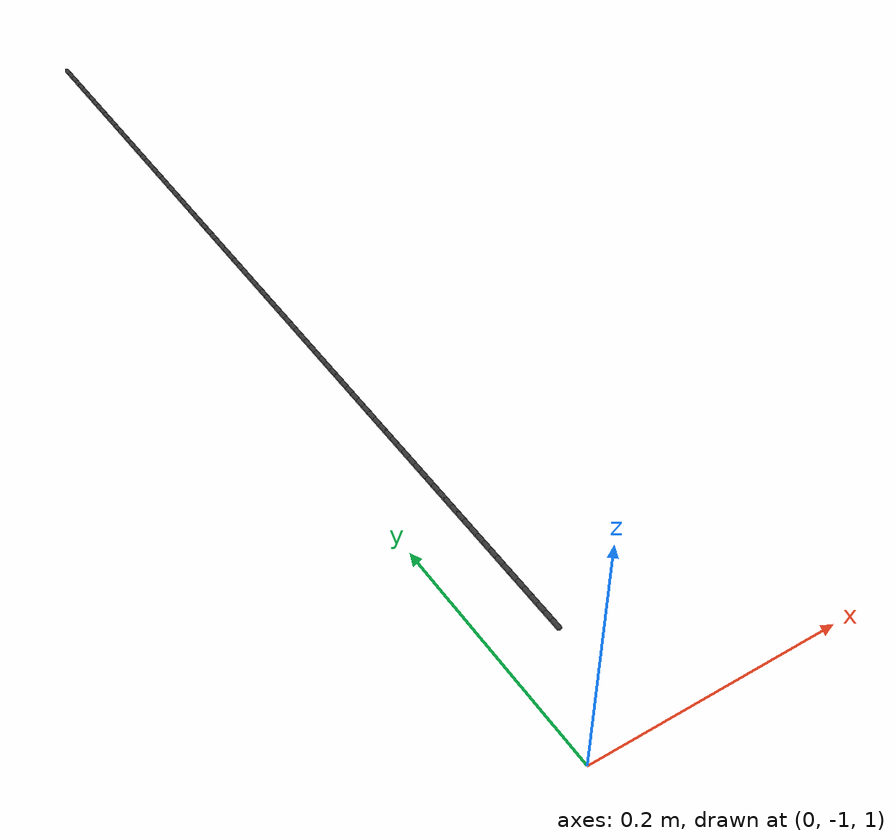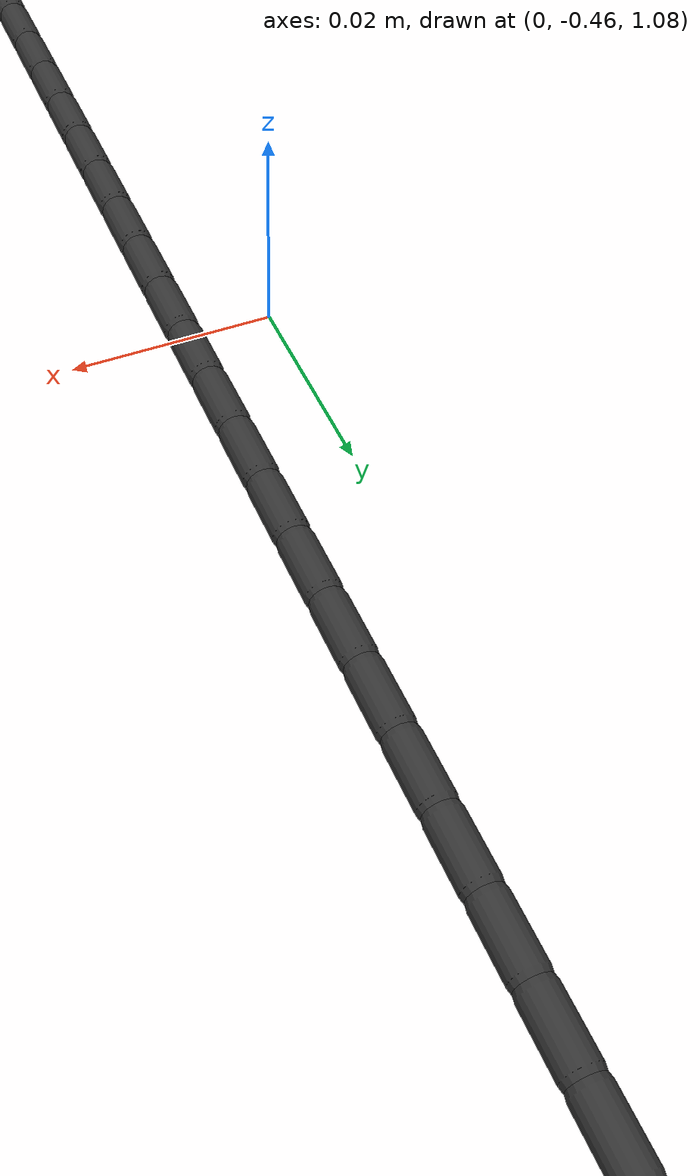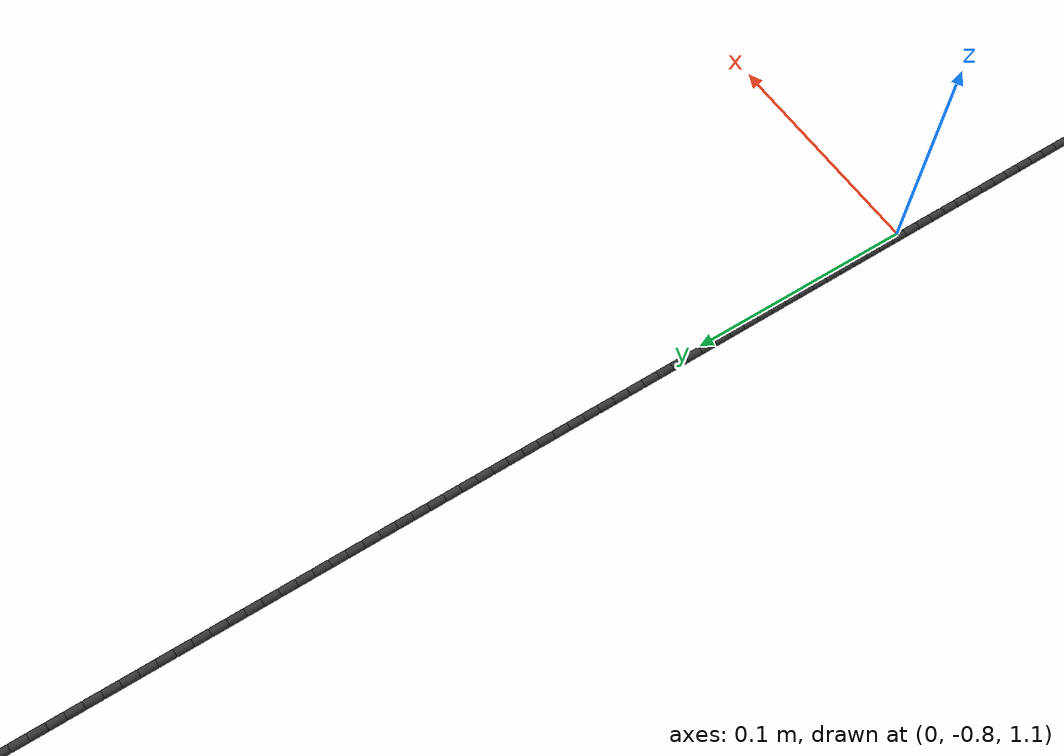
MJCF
<mujoco model="Catheter">
    <compiler angle="degree" />
    <size njmax="500" nconmax="500" />
    <default class="main">
        <default class="catheter">
            <motor ctrllimited="true"  forcelimited="true" ctrlrange="-1 1" forcerange="-1 1" />
			<joint pos="-0.00345 0 0"  group="3" limited="true" stiffness="1e-05" range="-20 20" armature="0.1" damping="0.005" />
			<geom size="0.0018 0.003"  quat="0.707107 0 0.707107 0" type="capsule" group="3" rgba="0.2 0.2 0.2 1" />
        </default>
        <default class="guidewire">
			<joint pos="-0.00345 0 0"  group="3" damping="0.005" stiffness="1e-05"/>
			<geom size="0.0018 0.003"  quat="0.707107 0 0.707107 0" type="capsule" group="3" rgba="0.2 0.2 0.2 1" />
        </default>
    </default>
    <worldbody>
        <body name="B0" pos="0.0076103 -0.95 1.07725" quat="0.707107 0 0 0.707107">
            <inertial pos="0 0 0" quat="0.707107 0 0.707107 0" mass="7.93943e-05" diaginertia="4.66839e-10 4.66839e-10 1.28619e-10" />
            <joint name="slider_joint" pos="0 0 0" axis="1 0 0" type="slide" limited="true" range="0 2" />
            <geom name="G0" size="0.0018 0.003" quat="0.707107 0 0.707107 0" type="capsule" group="1" rgba="0.2 0.2 0.2 1" />
            <body name="B1" pos="0.0072 0 0">
                <inertial pos="0 0 0" quat="0.707107 0 0.707107 0" mass="7.93943e-05" diaginertia="4.66839e-10 4.66839e-10 1.28619e-10" />
                <joint name="J0_1" axis="0 1 0" class="guidewire" />
                <joint name="J1_1" axis="0 0 1" class="guidewire" />
                <geom name="G1" size="0.0018 0.003" quat="0.707107 0 0.707107 0" type="capsule" group="1" rgba="0.2 0.2 0.2 1" />
                <body name="B2" pos="0.0072 0 0">
                    <inertial pos="0 0 0" quat="0.707107 0 0.707107 0" mass="7.93943e-05" diaginertia="4.66839e-10 4.66839e-10 1.28619e-10" />
                    <joint name="J0_2" axis="0 1 0" class="guidewire" />
                    <joint name="J1_2" axis="0 0 1" class="guidewire" />
                    <geom name="G2" size="0.0018 0.003" quat="0.707107 0 0.707107 0" type="capsule" group="1" rgba="0.2 0.2 0.2 1" />
                    <body name="B3" pos="0.0072 0 0">
                        <inertial pos="0 0 0" quat="0.707107 0 0.707107 0" mass="7.93943e-05" diaginertia="4.66839e-10 4.66839e-10 1.28619e-10" />
                        <joint name="J0_3" axis="0 1 0" class="guidewire" />
                        <joint name="J1_3" axis="0 0 1" class="guidewire" />
                        <geom name="G3" size="0.0018 0.003" quat="0.707107 0 0.707107 0" type="capsule" group="1" rgba="0.2 0.2 0.2 1" />
                        <body name="B4" pos="0.0072 0 0">
                            <inertial pos="0 0 0" quat="0.707107 0 0.707107 0" mass="7.93943e-05" diaginertia="4.66839e-10 4.66839e-10 1.28619e-10" />
                            <joint name="J0_4" axis="0 1 0" class="guidewire" />
                            <joint name="J1_4" axis="0 0 1" class="guidewire" />
                            <geom name="G4" size="0.0018 0.003" quat="0.707107 0 0.707107 0" type="capsule" group="1" rgba="0.2 0.2 0.2 1" />
                            <body name="B5" pos="0.0072 0 0">
                                <inertial pos="0 0 0" quat="0.707107 0 0.707107 0" mass="7.93943e-05" diaginertia="4.66839e-10 4.66839e-10 1.28619e-10" />
                                <joint name="J0_5" axis="0 1 0" class="guidewire" />
                                <joint name="J1_5" axis="0 0 1" class="guidewire" />
                                <geom name="G5" size="0.0018 0.003" quat="0.707107 0 0.707107 0" type="capsule" group="1" rgba="0.2 0.2 0.2 1" />
                                <body name="B6" pos="0.0072 0 0">
                                    <inertial pos="0 0 0" quat="0.707107 0 0.707107 0" mass="7.93943e-05" diaginertia="4.66839e-10 4.66839e-10 1.28619e-10" />
                                    <joint name="J0_6" axis="0 1 0" class="guidewire" />
                                    <joint name="J1_6" axis="0 0 1" class="guidewire" />
                                    <geom name="G6" size="0.0018 0.003" quat="0.707107 0 0.707107 0" type="capsule" group="1" rgba="0.2 0.2 0.2 1" />
                                    <body name="B7" pos="0.0072 0 0">
                                        <inertial pos="0 0 0" quat="0.707107 0 0.707107 0" mass="7.93943e-05" diaginertia="4.66839e-10 4.66839e-10 1.28619e-10" />
                                        <joint name="J0_7" axis="0 1 0" class="guidewire" />
                                        <joint name="J1_7" axis="0 0 1" class="guidewire" />
                                        <geom name="G7" size="0.0018 0.003" quat="0.707107 0 0.707107 0" type="capsule" group="1" rgba="0.2 0.2 0.2 1" />
                                        <body name="B8" pos="0.0072 0 0">
                                            <inertial pos="0 0 0" quat="0.707107 0 0.707107 0" mass="7.93943e-05" diaginertia="4.66839e-10 4.66839e-10 1.28619e-10" />
                                            <joint name="J0_8" axis="0 1 0" class="guidewire" />
                                            <joint name="J1_8" axis="0 0 1" class="guidewire" />
                                            <geom name="G8" size="0.0018 0.003" quat="0.707107 0 0.707107 0" type="capsule" group="1" rgba="0.2 0.2 0.2 1" />
                                            <body name="B9" pos="0.0072 0 0">
                                                <inertial pos="0 0 0" quat="0.707107 0 0.707107 0" mass="7.93943e-05" diaginertia="4.66839e-10 4.66839e-10 1.28619e-10" />
                                                <joint name="J0_9" axis="0 1 0" class="guidewire" />
                                                <joint name="J1_9" axis="0 0 1" class="guidewire" />
                                                <geom name="G9" size="0.0018 0.003" quat="0.707107 0 0.707107 0" type="capsule" group="1" rgba="0.2 0.2 0.2 1" />
                                                <body name="B10" pos="0.0072 0 0">
                                                    <inertial pos="0 0 0" quat="0.707107 0 0.707107 0" mass="7.93943e-05" diaginertia="4.66839e-10 4.66839e-10 1.28619e-10" />
                                                    <joint name="J0_10" axis="0 1 0" class="guidewire" />
                                                    <joint name="J1_10" axis="0 0 1" class="guidewire" />
                                                    <geom name="G10" size="0.0018 0.003" quat="0.707107 0 0.707107 0" type="capsule" group="1" rgba="0.2 0.2 0.2 1" />
                                                    <body name="B11" pos="0.0072 0 0">
                                                        <inertial pos="0 0 0" quat="0.707107 0 0.707107 0" mass="7.93943e-05" diaginertia="4.66839e-10 4.66839e-10 1.28619e-10" />
                                                        <joint name="J0_11" axis="0 1 0" class="guidewire" />
                                                        <joint name="J1_11" axis="0 0 1" class="guidewire" />
                                                        <geom name="G11" size="0.0018 0.003" quat="0.707107 0 0.707107 0" type="capsule" group="1" rgba="0.2 0.2 0.2 1" />
                                                        <body name="B12" pos="0.0072 0 0">
                                                            <inertial pos="0 0 0" quat="0.707107 0 0.707107 0" mass="7.93943e-05" diaginertia="4.66839e-10 4.66839e-10 1.28619e-10" />
                                                            <joint name="J0_12" axis="0 1 0" class="guidewire" />
                                                            <joint name="J1_12" axis="0 0 1" class="guidewire" />
                                                            <geom name="G12" size="0.0018 0.003" quat="0.707107 0 0.707107 0" type="capsule" group="1" rgba="0.2 0.2 0.2 1" />
                                                            <body name="B13" pos="0.0072 0 0">
                                                                <inertial pos="0 0 0" quat="0.707107 0 0.707107 0" mass="7.93943e-05" diaginertia="4.66839e-10 4.66839e-10 1.28619e-10" />
                                                                <joint name="J0_13" axis="0 1 0" class="guidewire" />
                                                                <joint name="J1_13" axis="0 0 1" class="guidewire" />
                                                                <geom name="G13" size="0.0018 0.003" quat="0.707107 0 0.707107 0" type="capsule" group="1" rgba="0.2 0.2 0.2 1" />
                                                                <body name="B14" pos="0.0072 0 0">
                                                                    <inertial pos="0 0 0" quat="0.707107 0 0.707107 0" mass="7.93943e-05" diaginertia="4.66839e-10 4.66839e-10 1.28619e-10" />
                                                                    <joint name="J0_14" axis="0 1 0" class="guidewire" />
                                                                    <joint name="J1_14" axis="0 0 1" class="guidewire" />
                                                                    <geom name="G14" size="0.0018 0.003" quat="0.707107 0 0.707107 0" type="capsule" group="1" rgba="0.2 0.2 0.2 1" />
                                                                    <body name="B15" pos="0.0072 0 0">
                                                                        <inertial pos="0 0 0" quat="0.707107 0 0.707107 0" mass="7.93943e-05" diaginertia="4.66839e-10 4.66839e-10 1.28619e-10" />
                                                                        <joint name="J0_15" axis="0 1 0" class="guidewire" />
                                                                        <joint name="J1_15" axis="0 0 1" class="guidewire" />
                                                                        <geom name="G15" size="0.0018 0.003" quat="0.707107 0 0.707107 0" type="capsule" group="1" rgba="0.2 0.2 0.2 1" />
                                                                        <body name="B16" pos="0.0072 0 0">
                                                                            <inertial pos="0 0 0" quat="0.707107 0 0.707107 0" mass="7.93943e-05" diaginertia="4.66839e-10 4.66839e-10 1.28619e-10" />
                                                                            <joint name="J0_16" axis="0 1 0" class="guidewire" />
                                                                            <joint name="J1_16" axis="0 0 1" class="guidewire" />
                                                                            <geom name="G16" size="0.0018 0.003" quat="0.707107 0 0.707107 0" type="capsule" group="1" rgba="0.2 0.2 0.2 1" />
                                                                            <body name="B17" pos="0.0072 0 0">
                                                                                <inertial pos="0 0 0" quat="0.707107 0 0.707107 0" mass="7.93943e-05" diaginertia="4.66839e-10 4.66839e-10 1.28619e-10" />
                                                                                <joint name="J0_17" axis="0 1 0" class="guidewire" />
                                                                                <joint name="J1_17" axis="0 0 1" class="guidewire" />
                                                                                <geom name="G17" size="0.0018 0.003" quat="0.707107 0 0.707107 0" type="capsule" group="1" rgba="0.2 0.2 0.2 1" />
                                                                                <body name="B18" pos="0.0072 0 0">
                                                                                    <inertial pos="0 0 0" quat="0.707107 0 0.707107 0" mass="7.93943e-05" diaginertia="4.66839e-10 4.66839e-10 1.28619e-10" />
                                                                                    <joint name="J0_18" axis="0 1 0" class="guidewire" />
                                                                                    <joint name="J1_18" axis="0 0 1" class="guidewire" />
                                                                                    <geom name="G18" size="0.0018 0.003" quat="0.707107 0 0.707107 0" type="capsule" group="1" rgba="0.2 0.2 0.2 1" />
                                                                                    <body name="B19" pos="0.0072 0 0">
                                                                                        <inertial pos="0 0 0" quat="0.707107 0 0.707107 0" mass="7.93943e-05" diaginertia="4.66839e-10 4.66839e-10 1.28619e-10" />
                                                                                        <joint name="J0_19" axis="0 1 0" class="guidewire" />
                                                                                        <joint name="J1_19" axis="0 0 1" class="guidewire" />
                                                                                        <geom name="G19" size="0.0018 0.003" quat="0.707107 0 0.707107 0" type="capsule" group="1" rgba="0.2 0.2 0.2 1" />
                                                                                        <body name="B20" pos="0.0072 0 0">
                                                                                            <inertial pos="0 0 0" quat="0.707107 0 0.707107 0" mass="7.93943e-05" diaginertia="4.66839e-10 4.66839e-10 1.28619e-10" />
                                                                                            <joint name="J0_20" axis="0 1 0" class="guidewire" />
                                                                                            <joint name="J1_20" axis="0 0 1" class="guidewire" />
                                                                                            <geom name="G20" size="0.0018 0.003" quat="0.707107 0 0.707107 0" type="capsule" group="1" rgba="0.2 0.2 0.2 1" />
                                                                                            <body name="B21" pos="0.0072 0 0">
                                                                                                <inertial pos="0 0 0" quat="0.707107 0 0.707107 0" mass="7.93943e-05" diaginertia="4.66839e-10 4.66839e-10 1.28619e-10" />
                                                                                                <joint name="J0_21" axis="0 1 0" class="guidewire" />
                                                                                                <joint name="J1_21" axis="0 0 1" class="guidewire" />
                                                                                                <geom name="G21" size="0.0018 0.003" quat="0.707107 0 0.707107 0" type="capsule" group="1" rgba="0.2 0.2 0.2 1" />
                                                                                                <body name="B22" pos="0.0072 0 0">
                                                                                                    <inertial pos="0 0 0" quat="0.707107 0 0.707107 0" mass="7.93943e-05" diaginertia="4.66839e-10 4.66839e-10 1.28619e-10" />
                                                                                                    <joint name="J0_22" axis="0 1 0" class="guidewire" />
                                                                                                    <joint name="J1_22" axis="0 0 1" class="guidewire" />
                                                                                                    <geom name="G22" size="0.0018 0.003" quat="0.707107 0 0.707107 0" type="capsule" group="1" rgba="0.2 0.2 0.2 1" />
                                                                                                    <body name="B23" pos="0.0072 0 0">
                                                                                                        <inertial pos="0 0 0" quat="0.707107 0 0.707107 0" mass="7.93943e-05" diaginertia="4.66839e-10 4.66839e-10 1.28619e-10" />
                                                                                                        <joint name="J0_23" axis="0 1 0" class="guidewire" />
                                                                                                        <joint name="J1_23" axis="0 0 1" class="guidewire" />
                                                                                                        <geom name="G23" size="0.0018 0.003" quat="0.707107 0 0.707107 0" type="capsule" group="1" rgba="0.2 0.2 0.2 1" />
                                                                                                        <body name="B24" pos="0.0072 0 0">
                                                                                                            <inertial pos="0 0 0" quat="0.707107 0 0.707107 0" mass="7.93943e-05" diaginertia="4.66839e-10 4.66839e-10 1.28619e-10" />
                                                                                                            <joint name="J0_24" axis="0 1 0" class="guidewire" />
                                                                                                            <joint name="J1_24" axis="0 0 1" class="guidewire" />
                                                                                                            <geom name="G24" size="0.0018 0.003" quat="0.707107 0 0.707107 0" type="capsule" group="1" rgba="0.2 0.2 0.2 1" />
                                                                                                            <body name="B25" pos="0.0072 0 0">
                                                                                                                <inertial pos="0 0 0" quat="0.707107 0 0.707107 0" mass="7.93943e-05" diaginertia="4.66839e-10 4.66839e-10 1.28619e-10" />
                                                                                                                <joint name="J0_25" axis="0 1 0" class="guidewire" />
                                                                                                                <joint name="J1_25" axis="0 0 1" class="guidewire" />
                                                                                                                <geom name="G25" size="0.0018 0.003" quat="0.707107 0 0.707107 0" type="capsule" group="1" rgba="0.2 0.2 0.2 1" />
                                                                                                                <body name="B26" pos="0.0072 0 0">
                                                                                                                    <inertial pos="0 0 0" quat="0.707107 0 0.707107 0" mass="7.93943e-05" diaginertia="4.66839e-10 4.66839e-10 1.28619e-10" />
                                                                                                                    <joint name="J0_26" axis="0 1 0" class="guidewire" />
                                                                                                                    <joint name="J1_26" axis="0 0 1" class="guidewire" />
                                                                                                                    <geom name="G26" size="0.0018 0.003" quat="0.707107 0 0.707107 0" type="capsule" group="1" rgba="0.2 0.2 0.2 1" />
                                                                                                                    <body name="B27" pos="0.0072 0 0">
                                                                                                                        <inertial pos="0 0 0" quat="0.707107 0 0.707107 0" mass="7.93943e-05" diaginertia="4.66839e-10 4.66839e-10 1.28619e-10" />
                                                                                                                        <joint name="J0_27" axis="0 1 0" class="guidewire" />
                                                                                                                        <joint name="J1_27" axis="0 0 1" class="guidewire" />
                                                                                                                        <geom name="G27" size="0.0018 0.003" quat="0.707107 0 0.707107 0" type="capsule" group="1" rgba="0.2 0.2 0.2 1" />
                                                                                                                        <body name="B28" pos="0.0072 0 0">
                                                                                                                            <inertial pos="0 0 0" quat="0.707107 0 0.707107 0" mass="7.93943e-05" diaginertia="4.66839e-10 4.66839e-10 1.28619e-10" />
                                                                                                                            <joint name="J0_28" axis="0 1 0" class="guidewire" />
                                                                                                                            <joint name="J1_28" axis="0 0 1" class="guidewire" />
                                                                                                                            <geom name="G28" size="0.0018 0.003" quat="0.707107 0 0.707107 0" type="capsule" group="1" rgba="0.2 0.2 0.2 1" />
                                                                                                                            <body name="B29" pos="0.0072 0 0">
                                                                                                                                <inertial pos="0 0 0" quat="0.707107 0 0.707107 0" mass="7.93943e-05" diaginertia="4.66839e-10 4.66839e-10 1.28619e-10" />
                                                                                                                                <joint name="J0_29" axis="0 1 0" class="guidewire" />
                                                                                                                                <joint name="J1_29" axis="0 0 1" class="guidewire" />
                                                                                                                                <geom name="G29" size="0.0018 0.003" quat="0.707107 0 0.707107 0" type="capsule" group="1" rgba="0.2 0.2 0.2 1" />
                                                                                                                                <body name="B30" pos="0.0072 0 0">
                                                                                                                                    <inertial pos="0 0 0" quat="0.707107 0 0.707107 0" mass="7.93943e-05" diaginertia="4.66839e-10 4.66839e-10 1.28619e-10" />
                                                                                                                                    <joint name="J0_30" axis="0 1 0" class="guidewire" />
                                                                                                                                    <joint name="J1_30" axis="0 0 1" class="guidewire" />
                                                                                                                                    <geom name="G30" size="0.0018 0.003" quat="0.707107 0 0.707107 0" type="capsule" group="1" rgba="0.2 0.2 0.2 1" />
                                                                                                                                    <body name="B31" pos="0.0072 0 0">
                                                                                                                                        <inertial pos="0 0 0" quat="0.707107 0 0.707107 0" mass="7.93943e-05" diaginertia="4.66839e-10 4.66839e-10 1.28619e-10" />
                                                                                                                                        <joint name="J0_31" axis="0 1 0" class="guidewire" />
                                                                                                                                        <joint name="J1_31" axis="0 0 1" class="guidewire" />
                                                                                                                                        <geom name="G31" size="0.0018 0.003" quat="0.707107 0 0.707107 0" type="capsule" group="1" rgba="0.2 0.2 0.2 1" />
                                                                                                                                        <body name="B32" pos="0.0072 0 0">
                                                                                                                                            <inertial pos="0 0 0" quat="0.707107 0 0.707107 0" mass="7.93943e-05" diaginertia="4.66839e-10 4.66839e-10 1.28619e-10" />
                                                                                                                                            <joint name="J0_32" axis="0 1 0" class="guidewire" />
                                                                                                                                            <joint name="J1_32" axis="0 0 1" class="guidewire" />
                                                                                                                                            <geom name="G32" size="0.0018 0.003" quat="0.707107 0 0.707107 0" type="capsule" group="1" rgba="0.2 0.2 0.2 1" />
                                                                                                                                            <body name="B33" pos="0.0072 0 0">
                                                                                                                                                <inertial pos="0 0 0" quat="0.707107 0 0.707107 0" mass="7.93943e-05" diaginertia="4.66839e-10 4.66839e-10 1.28619e-10" />
                                                                                                                                                <joint name="J0_33" axis="0 1 0" class="guidewire" />
                                                                                                                                                <joint name="J1_33" axis="0 0 1" class="guidewire" />
                                                                                                                                                <geom name="G33" size="0.0018 0.003" quat="0.707107 0 0.707107 0" type="capsule" group="1" rgba="0.2 0.2 0.2 1" />
                                                                                                                                                <body name="B34" pos="0.0072 0 0">
                                                                                                                                                    <inertial pos="0 0 0" quat="0.707107 0 0.707107 0" mass="7.93943e-05" diaginertia="4.66839e-10 4.66839e-10 1.28619e-10" />
                                                                                                                                                    <joint name="J0_34" axis="0 1 0" class="guidewire" />
                                                                                                                                                    <joint name="J1_34" axis="0 0 1" class="guidewire" />
                                                                                                                                                    <geom name="G34" size="0.0018 0.003" quat="0.707107 0 0.707107 0" type="capsule" group="1" rgba="0.2 0.2 0.2 1" />
                                                                                                                                                    <body name="B35" pos="0.0072 0 0">
                                                                                                                                                        <inertial pos="0 0 0" quat="0.707107 0 0.707107 0" mass="7.93943e-05" diaginertia="4.66839e-10 4.66839e-10 1.28619e-10" />
                                                                                                                                                        <joint name="J0_35" axis="0 1 0" class="guidewire" />
                                                                                                                                                        <joint name="J1_35" axis="0 0 1" class="guidewire" />
                                                                                                                                                        <geom name="G35" size="0.0018 0.003" quat="0.707107 0 0.707107 0" type="capsule" group="1" rgba="0.2 0.2 0.2 1" />
                                                                                                                                                        <body name="B36" pos="0.0072 0 0">
                                                                                                                                                            <inertial pos="0 0 0" quat="0.707107 0 0.707107 0" mass="7.93943e-05" diaginertia="4.66839e-10 4.66839e-10 1.28619e-10" />
                                                                                                                                                            <joint name="J0_36" axis="0 1 0" class="guidewire" />
                                                                                                                                                            <joint name="J1_36" axis="0 0 1" class="guidewire" />
                                                                                                                                                            <geom name="G36" size="0.0018 0.003" quat="0.707107 0 0.707107 0" type="capsule" group="1" rgba="0.2 0.2 0.2 1" />
                                                                                                                                                            <body name="B37" pos="0.0072 0 0">
                                                                                                                                                                <inertial pos="0 0 0" quat="0.707107 0 0.707107 0" mass="7.93943e-05" diaginertia="4.66839e-10 4.66839e-10 1.28619e-10" />
                                                                                                                                                                <joint name="J0_37" axis="0 1 0" class="guidewire" />
                                                                                                                                                                <joint name="J1_37" axis="0 0 1" class="guidewire" />
                                                                                                                                                                <geom name="G37" size="0.0018 0.003" quat="0.707107 0 0.707107 0" type="capsule" group="1" rgba="0.2 0.2 0.2 1" />
                                                                                                                                                                <body name="B38" pos="0.0072 0 0">
                                                                                                                                                                    <inertial pos="0 0 0" quat="0.707107 0 0.707107 0" mass="7.93943e-05" diaginertia="4.66839e-10 4.66839e-10 1.28619e-10" />
                                                                                                                                                                    <joint name="J0_38" axis="0 1 0" class="guidewire" />
                                                                                                                                                                    <joint name="J1_38" axis="0 0 1" class="guidewire" />
                                                                                                                                                                    <geom name="G38" size="0.0018 0.003" quat="0.707107 0 0.707107 0" type="capsule" group="1" rgba="0.2 0.2 0.2 1" />
                                                                                                                                                                    <body name="B39" pos="0.0072 0 0">
                                                                                                                                                                        <inertial pos="0 0 0" quat="0.707107 0 0.707107 0" mass="7.93943e-05" diaginertia="4.66839e-10 4.66839e-10 1.28619e-10" />
                                                                                                                                                                        <joint name="J0_39" axis="0 1 0" class="guidewire" />
                                                                                                                                                                        <joint name="J1_39" axis="0 0 1" class="guidewire" />
                                                                                                                                                                        <geom name="G39" size="0.0018 0.003" quat="0.707107 0 0.707107 0" type="capsule" group="1" rgba="0.2 0.2 0.2 1" />
                                                                                                                                                                        <body name="B40" pos="0.0072 0 0">
                                                                                                                                                                            <inertial pos="0 0 0" quat="0.707107 0 0.707107 0" mass="7.93943e-05" diaginertia="4.66839e-10 4.66839e-10 1.28619e-10" />
                                                                                                                                                                            <joint name="J0_40" axis="0 1 0" class="guidewire" />
                                                                                                                                                                            <joint name="J1_40" axis="0 0 1" class="guidewire" />
                                                                                                                                                                            <geom name="G40" size="0.0018 0.003" quat="0.707107 0 0.707107 0" type="capsule" group="1" rgba="0.2 0.2 0.2 1" />
                                                                                                                                                                            <body name="B41" pos="0.0072 0 0">
                                                                                                                                                                                <inertial pos="0 0 0" quat="0.707107 0 0.707107 0" mass="7.93943e-05" diaginertia="4.66839e-10 4.66839e-10 1.28619e-10" />
                                                                                                                                                                                <joint name="J0_41" axis="0 1 0" class="guidewire" />
                                                                                                                                                                                <joint name="J1_41" axis="0 0 1" class="guidewire" />
                                                                                                                                                                                <geom name="G41" size="0.0018 0.003" quat="0.707107 0 0.707107 0" type="capsule" group="1" rgba="0.2 0.2 0.2 1" />
                                                                                                                                                                                <body name="B42" pos="0.0072 0 0">
                                                                                                                                                                                    <inertial pos="0 0 0" quat="0.707107 0 0.707107 0" mass="7.93943e-05" diaginertia="4.66839e-10 4.66839e-10 1.28619e-10" />
                                                                                                                                                                                    <joint name="J0_42" axis="0 1 0" class="guidewire" />
                                                                                                                                                                                    <joint name="J1_42" axis="0 0 1" class="guidewire" />
                                                                                                                                                                                    <geom name="G42" size="0.0018 0.003" quat="0.707107 0 0.707107 0" type="capsule" group="1" rgba="0.2 0.2 0.2 1" />
                                                                                                                                                                                    <body name="B43" pos="0.0072 0 0">
                                                                                                                                                                                        <inertial pos="0 0 0" quat="0.707107 0 0.707107 0" mass="7.93943e-05" diaginertia="4.66839e-10 4.66839e-10 1.28619e-10" />
                                                                                                                                                                                        <joint name="J0_43" axis="0 1 0" class="guidewire" />
                                                                                                                                                                                        <joint name="J1_43" axis="0 0 1" class="guidewire" />
                                                                                                                                                                                        <geom name="G43" size="0.0018 0.003" quat="0.707107 0 0.707107 0" type="capsule" group="1" rgba="0.2 0.2 0.2 1" />
                                                                                                                                                                                        <body name="B44" pos="0.0072 0 0">
                                                                                                                                                                                            <inertial pos="0 0 0" quat="0.707107 0 0.707107 0" mass="7.93943e-05" diaginertia="4.66839e-10 4.66839e-10 1.28619e-10" />
                                                                                                                                                                                            <joint name="J0_44" axis="0 1 0" class="guidewire" />
                                                                                                                                                                                            <joint name="J1_44" axis="0 0 1" class="guidewire" />
                                                                                                                                                                                            <geom name="G44" size="0.0018 0.003" quat="0.707107 0 0.707107 0" type="capsule" group="1" rgba="0.2 0.2 0.2 1" />
                                                                                                                                                                                            <body name="B45" pos="0.0072 0 0">
                                                                                                                                                                                                <inertial pos="0 0 0" quat="0.707107 0 0.707107 0" mass="7.93943e-05" diaginertia="4.66839e-10 4.66839e-10 1.28619e-10" />
                                                                                                                                                                                                <joint name="J0_45" axis="0 1 0" class="guidewire" />
                                                                                                                                                                                                <joint name="J1_45" axis="0 0 1" class="guidewire" />
                                                                                                                                                                                                <geom name="G45" size="0.0018 0.003" quat="0.707107 0 0.707107 0" type="capsule" group="1" rgba="0.2 0.2 0.2 1" />
                                                                                                                                                                                                <body name="B46" pos="0.0072 0 0">
                                                                                                                                                                                                    <inertial pos="0 0 0" quat="0.707107 0 0.707107 0" mass="7.93943e-05" diaginertia="4.66839e-10 4.66839e-10 1.28619e-10" />
                                                                                                                                                                                                    <joint name="J0_46" axis="0 1 0" class="guidewire" />
                                                                                                                                                                                                    <joint name="J1_46" axis="0 0 1" class="guidewire" />
                                                                                                                                                                                                    <geom name="G46" size="0.0018 0.003" quat="0.707107 0 0.707107 0" type="capsule" group="1" rgba="0.2 0.2 0.2 1" />
                                                                                                                                                                                                    <body name="B47" pos="0.0072 0 0">
                                                                                                                                                                                                        <inertial pos="0 0 0" quat="0.707107 0 0.707107 0" mass="7.93943e-05" diaginertia="4.66839e-10 4.66839e-10 1.28619e-10" />
                                                                                                                                                                                                        <joint name="J0_47" axis="0 1 0" class="guidewire" />
                                                                                                                                                                                                        <joint name="J1_47" axis="0 0 1" class="guidewire" />
                                                                                                                                                                                                        <geom name="G47" size="0.0018 0.003" quat="0.707107 0 0.707107 0" type="capsule" group="1" rgba="0.2 0.2 0.2 1" />
                                                                                                                                                                                                        <body name="B48" pos="0.0072 0 0">
                                                                                                                                                                                                            <inertial pos="0 0 0" quat="0.707107 0 0.707107 0" mass="7.93943e-05" diaginertia="4.66839e-10 4.66839e-10 1.28619e-10" />
                                                                                                                                                                                                            <joint name="J0_48" axis="0 1 0" class="guidewire" />
                                                                                                                                                                                                            <joint name="J1_48" axis="0 0 1" class="guidewire" />
                                                                                                                                                                                                            <geom name="G48" size="0.0018 0.003" quat="0.707107 0 0.707107 0" type="capsule" group="1" rgba="0.2 0.2 0.2 1" />
                                                                                                                                                                                                            <body name="B49" pos="0.0072 0 0">
                                                                                                                                                                                                                <inertial pos="0 0 0" quat="0.707107 0 0.707107 0" mass="7.93943e-05" diaginertia="4.66839e-10 4.66839e-10 1.28619e-10" />
                                                                                                                                                                                                                <joint name="J0_49" axis="0 1 0" class="guidewire" />
                                                                                                                                                                                                                <joint name="J1_49" axis="0 0 1" class="guidewire" />
                                                                                                                                                                                                                <geom name="G49" size="0.0018 0.003" quat="0.707107 0 0.707107 0" type="capsule" group="1" rgba="0.2 0.2 0.2 1" />
                                                                                                                                                                                                                <body name="B50" pos="0.0072 0 0">
                                                                                                                                                                                                                    <inertial pos="0 0 0" quat="0.707107 0 0.707107 0" mass="7.93943e-05" diaginertia="4.66839e-10 4.66839e-10 1.28619e-10" />
                                                                                                                                                                                                                    <joint name="J0_50" axis="0 1 0" class="guidewire" />
                                                                                                                                                                                                                    <joint name="J1_50" axis="0 0 1" class="guidewire" />
                                                                                                                                                                                                                    <geom name="G50" size="0.0018 0.003" quat="0.707107 0 0.707107 0" type="capsule" group="1" rgba="0.2 0.2 0.2 1" />
                                                                                                                                                                                                                    <body name="B51" pos="0.0072 0 0">
                                                                                                                                                                                                                        <inertial pos="0 0 0" quat="0.707107 0 0.707107 0" mass="7.93943e-05" diaginertia="4.66839e-10 4.66839e-10 1.28619e-10" />
                                                                                                                                                                                                                        <joint name="J0_51" axis="0 1 0" class="guidewire" />
                                                                                                                                                                                                                        <joint name="J1_51" axis="0 0 1" class="guidewire" />
                                                                                                                                                                                                                        <geom name="G51" size="0.0018 0.003" quat="0.707107 0 0.707107 0" type="capsule" group="1" rgba="0.2 0.2 0.2 1" />
                                                                                                                                                                                                                        <body name="B52" pos="0.0072 0 0">
                                                                                                                                                                                                                            <inertial pos="0 0 0" quat="0.707107 0 0.707107 0" mass="7.93943e-05" diaginertia="4.66839e-10 4.66839e-10 1.28619e-10" />
                                                                                                                                                                                                                            <joint name="J0_52" axis="0 1 0" class="guidewire" />
                                                                                                                                                                                                                            <joint name="J1_52" axis="0 0 1" class="guidewire" />
                                                                                                                                                                                                                            <geom name="G52" size="0.0018 0.003" quat="0.707107 0 0.707107 0" type="capsule" group="1" rgba="0.2 0.2 0.2 1" />
                                                                                                                                                                                                                            <body name="B53" pos="0.0072 0 0">
                                                                                                                                                                                                                                <inertial pos="0 0 0" quat="0.707107 0 0.707107 0" mass="7.93943e-05" diaginertia="4.66839e-10 4.66839e-10 1.28619e-10" />
                                                                                                                                                                                                                                <joint name="J0_53" axis="0 1 0" class="guidewire" />
                                                                                                                                                                                                                                <joint name="J1_53" axis="0 0 1" class="guidewire" />
                                                                                                                                                                                                                                <geom name="G53" size="0.0018 0.003" quat="0.707107 0 0.707107 0" type="capsule" group="1" rgba="0.2 0.2 0.2 1" />
                                                                                                                                                                                                                                <body name="B54" pos="0.0072 0 0">
                                                                                                                                                                                                                                    <inertial pos="0 0 0" quat="0.707107 0 0.707107 0" mass="7.93943e-05" diaginertia="4.66839e-10 4.66839e-10 1.28619e-10" />
                                                                                                                                                                                                                                    <joint name="J0_54" axis="0 1 0" class="guidewire" />
                                                                                                                                                                                                                                    <joint name="J1_54" axis="0 0 1" class="guidewire" />
                                                                                                                                                                                                                                    <geom name="G54" size="0.0018 0.003" quat="0.707107 0 0.707107 0" type="capsule" group="1" rgba="0.2 0.2 0.2 1" />
                                                                                                                                                                                                                                    <body name="B55" pos="0.0072 0 0">
                                                                                                                                                                                                                                        <inertial pos="0 0 0" quat="0.707107 0 0.707107 0" mass="7.93943e-05" diaginertia="4.66839e-10 4.66839e-10 1.28619e-10" />
                                                                                                                                                                                                                                        <joint name="J0_55" axis="0 1 0" class="guidewire" />
                                                                                                                                                                                                                                        <joint name="J1_55" axis="0 0 1" class="guidewire" />
                                                                                                                                                                                                                                        <geom name="G55" size="0.0018 0.003" quat="0.707107 0 0.707107 0" type="capsule" group="1" rgba="0.2 0.2 0.2 1" />
                                                                                                                                                                                                                                        <body name="B56" pos="0.0072 0 0">
                                                                                                                                                                                                                                            <inertial pos="0 0 0" quat="0.707107 0 0.707107 0" mass="7.93943e-05" diaginertia="4.66839e-10 4.66839e-10 1.28619e-10" />
                                                                                                                                                                                                                                            <joint name="J0_56" axis="0 1 0" class="guidewire" />
                                                                                                                                                                                                                                            <joint name="J1_56" axis="0 0 1" class="guidewire" />
                                                                                                                                                                                                                                            <geom name="G56" size="0.0018 0.003" quat="0.707107 0 0.707107 0" type="capsule" group="1" rgba="0.2 0.2 0.2 1" />
                                                                                                                                                                                                                                            <body name="B57" pos="0.0072 0 0">
                                                                                                                                                                                                                                                <inertial pos="0 0 0" quat="0.707107 0 0.707107 0" mass="7.93943e-05" diaginertia="4.66839e-10 4.66839e-10 1.28619e-10" />
                                                                                                                                                                                                                                                <joint name="J0_57" axis="0 1 0" class="guidewire" />
                                                                                                                                                                                                                                                <joint name="J1_57" axis="0 0 1" class="guidewire" />
                                                                                                                                                                                                                                                <geom name="G57" size="0.0018 0.003" quat="0.707107 0 0.707107 0" type="capsule" group="1" rgba="0.2 0.2 0.2 1" />
                                                                                                                                                                                                                                                <body name="B58" pos="0.0072 0 0">
                                                                                                                                                                                                                                                    <inertial pos="0 0 0" quat="0.707107 0 0.707107 0" mass="7.93943e-05" diaginertia="4.66839e-10 4.66839e-10 1.28619e-10" />
                                                                                                                                                                                                                                                    <joint name="J0_58" axis="0 1 0" class="guidewire" />
                                                                                                                                                                                                                                                    <joint name="J1_58" axis="0 0 1" class="guidewire" />
                                                                                                                                                                                                                                                    <geom name="G58" size="0.0018 0.003" quat="0.707107 0 0.707107 0" type="capsule" group="1" rgba="0.2 0.2 0.2 1" />
                                                                                                                                                                                                                                                    <body name="B59" pos="0.0072 0 0">
                                                                                                                                                                                                                                                        <inertial pos="0 0 0" quat="0.707107 0 0.707107 0" mass="7.93943e-05" diaginertia="4.66839e-10 4.66839e-10 1.28619e-10" />
                                                                                                                                                                                                                                                        <joint name="J0_59" axis="0 1 0" class="guidewire" />
                                                                                                                                                                                                                                                        <joint name="J1_59" axis="0 0 1" class="guidewire" />
                                                                                                                                                                                                                                                        <geom name="G59" size="0.0018 0.003" quat="0.707107 0 0.707107 0" type="capsule" group="1" rgba="0.2 0.2 0.2 1" />
                                                                                                                                                                                                                                                        <body name="B60" pos="0.0072 0 0">
                                                                                                                                                                                                                                                            <inertial pos="0 0 0" quat="0.707107 0 0.707107 0" mass="7.93943e-05" diaginertia="4.66839e-10 4.66839e-10 1.28619e-10" />
                                                                                                                                                                                                                                                            <joint name="J0_60" axis="0 1 0" class="guidewire" />
                                                                                                                                                                                                                                                            <joint name="J1_60" axis="0 0 1" class="guidewire" />
                                                                                                                                                                                                                                                            <geom name="G60" size="0.0018 0.003" quat="0.707107 0 0.707107 0" type="capsule" group="1" rgba="0.2 0.2 0.2 1" />
                                                                                                                                                                                                                                                            <body name="B61" pos="0.0072 0 0">
                                                                                                                                                                                                                                                                <inertial pos="0 0 0" quat="0.707107 0 0.707107 0" mass="7.93943e-05" diaginertia="4.66839e-10 4.66839e-10 1.28619e-10" />
                                                                                                                                                                                                                                                                <joint name="J0_61" axis="0 1 0" class="guidewire" />
                                                                                                                                                                                                                                                                <joint name="J1_61" axis="0 0 1" class="guidewire" />
                                                                                                                                                                                                                                                                <geom name="G61" size="0.0018 0.003" quat="0.707107 0 0.707107 0" type="capsule" group="1" rgba="0.2 0.2 0.2 1" />
                                                                                                                                                                                                                                                                <body name="B62" pos="0.0072 0 0">
                                                                                                                                                                                                                                                                    <inertial pos="0 0 0" quat="0.707107 0 0.707107 0" mass="7.93943e-05" diaginertia="4.66839e-10 4.66839e-10 1.28619e-10" />
                                                                                                                                                                                                                                                                    <joint name="J0_62" axis="0 1 0" class="guidewire" />
                                                                                                                                                                                                                                                                    <joint name="J1_62" axis="0 0 1" class="guidewire" />
                                                                                                                                                                                                                                                                    <geom name="G62" size="0.0018 0.003" quat="0.707107 0 0.707107 0" type="capsule" group="1" rgba="0.2 0.2 0.2 1" />
                                                                                                                                                                                                                                                                    <body name="B63" pos="0.0072 0 0">
                                                                                                                                                                                                                                                                        <inertial pos="0 0 0" quat="0.707107 0 0.707107 0" mass="7.93943e-05" diaginertia="4.66839e-10 4.66839e-10 1.28619e-10" />
                                                                                                                                                                                                                                                                        <joint name="J0_63" axis="0 1 0" class="guidewire" />
                                                                                                                                                                                                                                                                        <joint name="J1_63" axis="0 0 1" class="guidewire" />
                                                                                                                                                                                                                                                                        <geom name="G63" size="0.0018 0.003" quat="0.707107 0 0.707107 0" type="capsule" group="1" rgba="0.2 0.2 0.2 1" />
                                                                                                                                                                                                                                                                        <body name="B64" pos="0.0072 0 0">
                                                                                                                                                                                                                                                                            <inertial pos="0 0 0" quat="0.707107 0 0.707107 0" mass="7.93943e-05" diaginertia="4.66839e-10 4.66839e-10 1.28619e-10" />
                                                                                                                                                                                                                                                                            <joint name="J0_64" axis="0 1 0" class="guidewire" />
                                                                                                                                                                                                                                                                            <joint name="J1_64" axis="0 0 1" class="guidewire" />
                                                                                                                                                                                                                                                                            <geom name="G64" size="0.0018 0.003" quat="0.707107 0 0.707107 0" type="capsule" group="1" rgba="0.2 0.2 0.2 1" />
                                                                                                                                                                                                                                                                            <body name="B65" pos="0.0072 0 0">
                                                                                                                                                                                                                                                                                <inertial pos="0 0 0" quat="0.707107 0 0.707107 0" mass="7.93943e-05" diaginertia="4.66839e-10 4.66839e-10 1.28619e-10" />
                                                                                                                                                                                                                                                                                <joint name="J0_65" axis="0 1 0" class="guidewire" />
                                                                                                                                                                                                                                                                                <joint name="J1_65" axis="0 0 1" class="guidewire" />
                                                                                                                                                                                                                                                                                <geom name="G65" size="0.0018 0.003" quat="0.707107 0 0.707107 0" type="capsule" group="1" rgba="0.2 0.2 0.2 1" />
                                                                                                                                                                                                                                                                                <body name="B66" pos="0.0072 0 0">
                                                                                                                                                                                                                                                                                    <inertial pos="0 0 0" quat="0.707107 0 0.707107 0" mass="7.93943e-05" diaginertia="4.66839e-10 4.66839e-10 1.28619e-10" />
                                                                                                                                                                                                                                                                                    <joint name="J0_66" axis="0 1 0" class="guidewire" />
                                                                                                                                                                                                                                                                                    <joint name="J1_66" axis="0 0 1" class="guidewire" />
                                                                                                                                                                                                                                                                                    <geom name="G66" size="0.0018 0.003" quat="0.707107 0 0.707107 0" type="capsule" group="1" rgba="0.2 0.2 0.2 1" />
                                                                                                                                                                                                                                                                                    <body name="B67" pos="0.0072 0 0">
                                                                                                                                                                                                                                                                                        <inertial pos="0 0 0" quat="0.707107 0 0.707107 0" mass="7.93943e-05" diaginertia="4.66839e-10 4.66839e-10 1.28619e-10" />
                                                                                                                                                                                                                                                                                        <joint name="J0_67" axis="0 1 0" class="guidewire" />
                                                                                                                                                                                                                                                                                        <joint name="J1_67" axis="0 0 1" class="guidewire" />
                                                                                                                                                                                                                                                                                        <geom name="G67" size="0.0018 0.003" quat="0.707107 0 0.707107 0" type="capsule" group="1" rgba="0.2 0.2 0.2 1" />
                                                                                                                                                                                                                                                                                        <body name="B68" pos="0.0072 0 0">
                                                                                                                                                                                                                                                                                            <inertial pos="0 0 0" quat="0.707107 0 0.707107 0" mass="7.93943e-05" diaginertia="4.66839e-10 4.66839e-10 1.28619e-10" />
                                                                                                                                                                                                                                                                                            <joint name="J0_68" axis="0 1 0" class="guidewire" />
                                                                                                                                                                                                                                                                                            <joint name="J1_68" axis="0 0 1" class="guidewire" />
                                                                                                                                                                                                                                                                                            <geom name="G68" size="0.0018 0.003" quat="0.707107 0 0.707107 0" type="capsule" group="1" rgba="0.2 0.2 0.2 1" />
                                                                                                                                                                                                                                                                                            <body name="B69" pos="0.0072 0 0">
                                                                                                                                                                                                                                                                                                <inertial pos="0 0 0" quat="0.707107 0 0.707107 0" mass="7.93943e-05" diaginertia="4.66839e-10 4.66839e-10 1.28619e-10" />
                                                                                                                                                                                                                                                                                                <joint name="J0_69" axis="0 1 0" class="guidewire" />
                                                                                                                                                                                                                                                                                                <joint name="J1_69" axis="0 0 1" class="guidewire" />
                                                                                                                                                                                                                                                                                                <geom name="G69" size="0.0018 0.003" quat="0.707107 0 0.707107 0" type="capsule" group="1" rgba="0.2 0.2 0.2 1" />
                                                                                                                                                                                                                                                                                                <body name="B70" pos="0.0072 0 0">
                                                                                                                                                                                                                                                                                                    <inertial pos="0 0 0" quat="0.707107 0 0.707107 0" mass="7.93943e-05" diaginertia="4.66839e-10 4.66839e-10 1.28619e-10" />
                                                                                                                                                                                                                                                                                                    <joint name="J0_70" axis="0 1 0" class="guidewire" />
                                                                                                                                                                                                                                                                                                    <joint name="J1_70" axis="0 0 1" class="guidewire" />
                                                                                                                                                                                                                                                                                                    <geom name="G70" size="0.0018 0.003" quat="0.707107 0 0.707107 0" type="capsule" group="1" rgba="0.2 0.2 0.2 1" />
                                                                                                                                                                                                                                                                                                    <body name="B71" pos="0.0072 0 0">
                                                                                                                                                                                                                                                                                                        <inertial pos="0 0 0" quat="0.707107 0 0.707107 0" mass="7.93943e-05" diaginertia="4.66839e-10 4.66839e-10 1.28619e-10" />
                                                                                                                                                                                                                                                                                                        <joint name="J0_71" axis="0 1 0" class="guidewire" />
                                                                                                                                                                                                                                                                                                        <joint name="J1_71" axis="0 0 1" class="guidewire" />
                                                                                                                                                                                                                                                                                                        <geom name="G71" size="0.0018 0.003" quat="0.707107 0 0.707107 0" type="capsule" group="1" rgba="0.2 0.2 0.2 1" />
                                                                                                                                                                                                                                                                                                        <body name="B72" pos="0.0072 0 0">
                                                                                                                                                                                                                                                                                                            <inertial pos="0 0 0" quat="0.707107 0 0.707107 0" mass="7.93943e-05" diaginertia="4.66839e-10 4.66839e-10 1.28619e-10" />
                                                                                                                                                                                                                                                                                                            <joint name="J0_72" axis="0 1 0" class="guidewire" />
                                                                                                                                                                                                                                                                                                            <joint name="J1_72" axis="0 0 1" class="guidewire" />
                                                                                                                                                                                                                                                                                                            <geom name="G72" size="0.0018 0.003" quat="0.707107 0 0.707107 0" type="capsule" group="1" rgba="0.2 0.2 0.2 1" />
                                                                                                                                                                                                                                                                                                            <body name="B73" pos="0.0072 0 0">
                                                                                                                                                                                                                                                                                                                <inertial pos="0 0 0" quat="0.707107 0 0.707107 0" mass="7.93943e-05" diaginertia="4.66839e-10 4.66839e-10 1.28619e-10" />
                                                                                                                                                                                                                                                                                                                <joint name="J0_73" axis="0 1 0" class="guidewire" />
                                                                                                                                                                                                                                                                                                                <joint name="J1_73" axis="0 0 1" class="guidewire" />
                                                                                                                                                                                                                                                                                                                <geom name="G73" size="0.0018 0.003" quat="0.707107 0 0.707107 0" type="capsule" group="1" rgba="0.2 0.2 0.2 1" />
                                                                                                                                                                                                                                                                                                                <body name="B74" pos="0.0072 0 0">
                                                                                                                                                                                                                                                                                                                    <inertial pos="0 0 0" quat="0.707107 0 0.707107 0" mass="7.93943e-05" diaginertia="4.66839e-10 4.66839e-10 1.28619e-10" />
                                                                                                                                                                                                                                                                                                                    <joint name="J0_74" axis="0 1 0" class="guidewire" />
                                                                                                                                                                                                                                                                                                                    <joint name="J1_74" axis="0 0 1" class="guidewire" />
                                                                                                                                                                                                                                                                                                                    <geom name="G74" size="0.0018 0.003" quat="0.707107 0 0.707107 0" type="capsule" group="1" rgba="0.2 0.2 0.2 1" />
                                                                                                                                                                                                                                                                                                                    <body name="B75" pos="0.0072 0 0">
                                                                                                                                                                                                                                                                                                                        <inertial pos="0 0 0" quat="0.707107 0 0.707107 0" mass="7.93943e-05" diaginertia="4.66839e-10 4.66839e-10 1.28619e-10" />
                                                                                                                                                                                                                                                                                                                        <joint name="J0_75" axis="0 1 0" class="guidewire" />
                                                                                                                                                                                                                                                                                                                        <joint name="J1_75" axis="0 0 1" class="guidewire" />
                                                                                                                                                                                                                                                                                                                        <geom name="G75" size="0.0018 0.003" quat="0.707107 0 0.707107 0" type="capsule" group="1" rgba="0.2 0.2 0.2 1" />
                                                                                                                                                                                                                                                                                                                        <body name="B76" pos="0.0072 0 0">
                                                                                                                                                                                                                                                                                                                            <inertial pos="0 0 0" quat="0.707107 0 0.707107 0" mass="7.93943e-05" diaginertia="4.66839e-10 4.66839e-10 1.28619e-10" />
                                                                                                                                                                                                                                                                                                                            <joint name="J0_76" axis="0 1 0" class="guidewire" />
                                                                                                                                                                                                                                                                                                                            <joint name="J1_76" axis="0 0 1" class="guidewire" />
                                                                                                                                                                                                                                                                                                                            <geom name="G76" size="0.0018 0.003" quat="0.707107 0 0.707107 0" type="capsule" group="1" rgba="0.2 0.2 0.2 1" />
                                                                                                                                                                                                                                                                                                                            <body name="B77" pos="0.0072 0 0">
                                                                                                                                                                                                                                                                                                                                <inertial pos="0 0 0" quat="0.707107 0 0.707107 0" mass="7.93943e-05" diaginertia="4.66839e-10 4.66839e-10 1.28619e-10" />
                                                                                                                                                                                                                                                                                                                                <joint name="J0_77" axis="0 1 0" class="guidewire" />
                                                                                                                                                                                                                                                                                                                                <joint name="J1_77" axis="0 0 1" class="guidewire" />
                                                                                                                                                                                                                                                                                                                                <geom name="G77" size="0.0018 0.003" quat="0.707107 0 0.707107 0" type="capsule" group="1" rgba="0.2 0.2 0.2 1" />
                                                                                                                                                                                                                                                                                                                                <body name="B78" pos="0.0072 0 0">
                                                                                                                                                                                                                                                                                                                                    <inertial pos="0 0 0" quat="0.707107 0 0.707107 0" mass="7.93943e-05" diaginertia="4.66839e-10 4.66839e-10 1.28619e-10" />
                                                                                                                                                                                                                                                                                                                                    <joint name="J0_78" axis="0 1 0" class="guidewire" />
                                                                                                                                                                                                                                                                                                                                    <joint name="J1_78" axis="0 0 1" class="guidewire" />
                                                                                                                                                                                                                                                                                                                                    <geom name="G78" size="0.0018 0.003" quat="0.707107 0 0.707107 0" type="capsule" group="1" rgba="0.2 0.2 0.2 1" />
                                                                                                                                                                                                                                                                                                                                    <body name="B79" pos="0.0072 0 0">
                                                                                                                                                                                                                                                                                                                                        <inertial pos="0 0 0" quat="0.707107 0 0.707107 0" mass="7.93943e-05" diaginertia="4.66839e-10 4.66839e-10 1.28619e-10" />
                                                                                                                                                                                                                                                                                                                                        <joint name="J0_79" axis="0 1 0" class="guidewire" />
                                                                                                                                                                                                                                                                                                                                        <joint name="J1_79" axis="0 0 1" class="guidewire" />
                                                                                                                                                                                                                                                                                                                                        <geom name="G79" size="0.0018 0.003" quat="0.707107 0 0.707107 0" type="capsule" group="1" rgba="0.2 0.2 0.2 1" />
                                                                                                                                                                                                                                                                                                                                        <body name="B80" pos="0.0072 0 0">
                                                                                                                                                                                                                                                                                                                                            <inertial pos="0 0 0" quat="0.707107 0 0.707107 0" mass="7.93943e-05" diaginertia="4.66839e-10 4.66839e-10 1.28619e-10" />
                                                                                                                                                                                                                                                                                                                                            <joint name="J0_80" axis="0 1 0" class="guidewire" />
                                                                                                                                                                                                                                                                                                                                            <joint name="J1_80" axis="0 0 1" class="guidewire" />
                                                                                                                                                                                                                                                                                                                                            <geom name="G80" size="0.0018 0.003" quat="0.707107 0 0.707107 0" type="capsule" group="1" rgba="0.2 0.2 0.2 1" />
                                                                                                                                                                                                                                                                                                                                            <body name="B81" pos="0.0072 0 0">
                                                                                                                                                                                                                                                                                                                                                <inertial pos="0 0 0" quat="0.707107 0 0.707107 0" mass="7.93943e-05" diaginertia="4.66839e-10 4.66839e-10 1.28619e-10" />
                                                                                                                                                                                                                                                                                                                                                <joint name="J0_81" axis="0 1 0" class="guidewire" />
                                                                                                                                                                                                                                                                                                                                                <joint name="J1_81" axis="0 0 1" class="guidewire" />
                                                                                                                                                                                                                                                                                                                                                <geom name="G81" size="0.0018 0.003" quat="0.707107 0 0.707107 0" type="capsule" group="1" rgba="0.2 0.2 0.2 1" />
                                                                                                                                                                                                                                                                                                                                                <body name="B82" pos="0.0072 0 0">
                                                                                                                                                                                                                                                                                                                                                    <inertial pos="0 0 0" quat="0.707107 0 0.707107 0" mass="7.93943e-05" diaginertia="4.66839e-10 4.66839e-10 1.28619e-10" />
                                                                                                                                                                                                                                                                                                                                                    <joint name="J0_82" axis="0 1 0" class="guidewire" />
                                                                                                                                                                                                                                                                                                                                                    <joint name="J1_82" axis="0 0 1" class="guidewire" />
                                                                                                                                                                                                                                                                                                                                                    <geom name="G82" size="0.0018 0.003" quat="0.707107 0 0.707107 0" type="capsule" group="1" rgba="0.2 0.2 0.2 1" />
                                                                                                                                                                                                                                                                                                                                                    <body name="B83" pos="0.0072 0 0">
                                                                                                                                                                                                                                                                                                                                                        <inertial pos="0 0 0" quat="0.707107 0 0.707107 0" mass="7.93943e-05" diaginertia="4.66839e-10 4.66839e-10 1.28619e-10" />
                                                                                                                                                                                                                                                                                                                                                        <joint name="J0_83" axis="0 1 0" class="guidewire" />
                                                                                                                                                                                                                                                                                                                                                        <joint name="J1_83" axis="0 0 1" class="guidewire" />
                                                                                                                                                                                                                                                                                                                                                        <geom name="G83" size="0.0018 0.003" quat="0.707107 0 0.707107 0" type="capsule" group="1" rgba="0.2 0.2 0.2 1" />
                                                                                                                                                                                                                                                                                                                                                        <body name="B84" pos="0.0072 0 0">
                                                                                                                                                                                                                                                                                                                                                            <inertial pos="0 0 0" quat="0.707107 0 0.707107 0" mass="7.93943e-05" diaginertia="4.66839e-10 4.66839e-10 1.28619e-10" />
                                                                                                                                                                                                                                                                                                                                                            <joint name="J0_84" axis="0 1 0" class="guidewire" />
                                                                                                                                                                                                                                                                                                                                                            <joint name="J1_84" axis="0 0 1" class="guidewire" />
                                                                                                                                                                                                                                                                                                                                                            <geom name="G84" size="0.0018 0.003" quat="0.707107 0 0.707107 0" type="capsule" group="1" rgba="0.2 0.2 0.2 1" />
                                                                                                                                                                                                                                                                                                                                                            <body name="B85" pos="0.0072 0 0">
                                                                                                                                                                                                                                                                                                                                                                <inertial pos="0 0 0" quat="0.707107 0 0.707107 0" mass="7.93943e-05" diaginertia="4.66839e-10 4.66839e-10 1.28619e-10" />
                                                                                                                                                                                                                                                                                                                                                                <joint name="J0_85" axis="0 1 0" class="guidewire" />
                                                                                                                                                                                                                                                                                                                                                                <joint name="J1_85" axis="0 0 1" class="guidewire" />
                                                                                                                                                                                                                                                                                                                                                                <geom name="G85" size="0.0018 0.003" quat="0.707107 0 0.707107 0" type="capsule" group="1" rgba="0.2 0.2 0.2 1" />
                                                                                                                                                                                                                                                                                                                                                                <body name="B86" pos="0.0072 0 0">
                                                                                                                                                                                                                                                                                                                                                                    <inertial pos="0 0 0" quat="0.707107 0 0.707107 0" mass="7.93943e-05" diaginertia="4.66839e-10 4.66839e-10 1.28619e-10" />
                                                                                                                                                                                                                                                                                                                                                                    <joint name="J0_86" axis="0 1 0" class="guidewire" />
                                                                                                                                                                                                                                                                                                                                                                    <joint name="J1_86" axis="0 0 1" class="guidewire" />
                                                                                                                                                                                                                                                                                                                                                                    <geom name="G86" size="0.0018 0.003" quat="0.707107 0 0.707107 0" type="capsule" group="1" rgba="0.2 0.2 0.2 1" />
                                                                                                                                                                                                                                                                                                                                                                    <body name="B87" pos="0.0072 0 0">
                                                                                                                                                                                                                                                                                                                                                                        <inertial pos="0 0 0" quat="0.707107 0 0.707107 0" mass="7.93943e-05" diaginertia="4.66839e-10 4.66839e-10 1.28619e-10" />
                                                                                                                                                                                                                                                                                                                                                                        <joint name="J0_87" axis="0 1 0" class="guidewire" />
                                                                                                                                                                                                                                                                                                                                                                        <joint name="J1_87" axis="0 0 1" class="guidewire" />
                                                                                                                                                                                                                                                                                                                                                                        <geom name="G87" size="0.0018 0.003" quat="0.707107 0 0.707107 0" type="capsule" group="1" rgba="0.2 0.2 0.2 1" />
                                                                                                                                                                                                                                                                                                                                                                        <body name="B88" pos="0.0072 0 0">
                                                                                                                                                                                                                                                                                                                                                                            <inertial pos="0 0 0" quat="0.707107 0 0.707107 0" mass="7.93943e-05" diaginertia="4.66839e-10 4.66839e-10 1.28619e-10" />
                                                                                                                                                                                                                                                                                                                                                                            <joint name="J0_88" axis="0 1 0" class="guidewire" />
                                                                                                                                                                                                                                                                                                                                                                            <joint name="J1_88" axis="0 0 1" class="guidewire" />
                                                                                                                                                                                                                                                                                                                                                                            <geom name="G88" size="0.0018 0.003" quat="0.707107 0 0.707107 0" type="capsule" group="1" rgba="0.2 0.2 0.2 1" />
                                                                                                                                                                                                                                                                                                                                                                            <body name="B89" pos="0.0072 0 0">
                                                                                                                                                                                                                                                                                                                                                                                <inertial pos="0 0 0" quat="0.707107 0 0.707107 0" mass="7.93943e-05" diaginertia="4.66839e-10 4.66839e-10 1.28619e-10" />
                                                                                                                                                                                                                                                                                                                                                                                <joint name="J0_89" axis="0 1 0" class="guidewire" />
                                                                                                                                                                                                                                                                                                                                                                                <joint name="J1_89" axis="0 0 1" class="guidewire" />
                                                                                                                                                                                                                                                                                                                                                                                <geom name="G89" size="0.0018 0.003" quat="0.707107 0 0.707107 0" type="capsule" group="1" rgba="0.2 0.2 0.2 1" />
                                                                                                                                                                                                                                                                                                                                                                                <body name="B90" pos="0.0072 0 0">
                                                                                                                                                                                                                                                                                                                                                                                    <inertial pos="0 0 0" quat="0.707107 0 0.707107 0" mass="7.93943e-05" diaginertia="4.66839e-10 4.66839e-10 1.28619e-10" />
                                                                                                                                                                                                                                                                                                                                                                                    <joint name="J0_90" axis="0 1 0" class="catheter" />
                                                                                                                                                                                                                                                                                                                                                                                    <joint name="J1_90" axis="0 0 1" class="catheter" />
                                                                                                                                                                                                                                                                                                                                                                                    <geom name="G90" size="0.0018 0.003" quat="0.707107 0 0.707107 0" type="capsule" group="1" rgba="0.2 0.2 0.2 1" />
                                                                                                                                                                                                                                                                                                                                                                                    <body name="B91" pos="0.0072 0 0">
                                                                                                                                                                                                                                                                                                                                                                                        <inertial pos="0 0 0" quat="0.707107 0 0.707107 0" mass="7.93943e-05" diaginertia="4.66839e-10 4.66839e-10 1.28619e-10" />
                                                                                                                                                                                                                                                                                                                                                                                        <joint name="J0_91" axis="0 1 0" class="catheter" />
                                                                                                                                                                                                                                                                                                                                                                                        <joint name="J1_91" axis="0 0 1" class="catheter" />
                                                                                                                                                                                                                                                                                                                                                                                        <geom name="G91" size="0.0018 0.003" quat="0.707107 0 0.707107 0" type="capsule" group="1" rgba="0.2 0.2 0.2 1" />
                                                                                                                                                                                                                                                                                                                                                                                        <body name="B92" pos="0.0072 0 0">
                                                                                                                                                                                                                                                                                                                                                                                            <inertial pos="0 0 0" quat="0.707107 0 0.707107 0" mass="7.93943e-05" diaginertia="4.66839e-10 4.66839e-10 1.28619e-10" />
                                                                                                                                                                                                                                                                                                                                                                                            <joint name="J0_92" axis="0 1 0" class="catheter" />
                                                                                                                                                                                                                                                                                                                                                                                            <joint name="J1_92" axis="0 0 1" class="catheter" />
                                                                                                                                                                                                                                                                                                                                                                                            <geom name="G92" size="0.0018 0.003" quat="0.707107 0 0.707107 0" type="capsule" group="1" rgba="0.2 0.2 0.2 1" />
                                                                                                                                                                                                                                                                                                                                                                                            <body name="B93" pos="0.0072 0 0">
                                                                                                                                                                                                                                                                                                                                                                                                <inertial pos="0 0 0" quat="0.707107 0 0.707107 0" mass="7.93943e-05" diaginertia="4.66839e-10 4.66839e-10 1.28619e-10" />
                                                                                                                                                                                                                                                                                                                                                                                                <joint name="J0_93" axis="0 1 0" class="catheter" />
                                                                                                                                                                                                                                                                                                                                                                                                <joint name="J1_93" axis="0 0 1" class="catheter" />
                                                                                                                                                                                                                                                                                                                                                                                                <geom name="G93" size="0.0018 0.003" quat="0.707107 0 0.707107 0" type="capsule" group="1" rgba="0.2 0.2 0.2 1" />
                                                                                                                                                                                                                                                                                                                                                                                                <body name="B94" pos="0.0072 0 0">
                                                                                                                                                                                                                                                                                                                                                                                                    <inertial pos="0 0 0" quat="0.707107 0 0.707107 0" mass="7.93943e-05" diaginertia="4.66839e-10 4.66839e-10 1.28619e-10" />
                                                                                                                                                                                                                                                                                                                                                                                                    <joint name="J0_94" axis="0 1 0" class="catheter" />
                                                                                                                                                                                                                                                                                                                                                                                                    <joint name="J1_94" axis="0 0 1" class="catheter" />
                                                                                                                                                                                                                                                                                                                                                                                                    <geom name="G94" size="0.0018 0.003" quat="0.707107 0 0.707107 0" type="capsule" group="1" rgba="0.2 0.2 0.2 1" />
                                                                                                                                                                                                                                                                                                                                                                                                    <body name="B95" pos="0.0072 0 0">
                                                                                                                                                                                                                                                                                                                                                                                                        <inertial pos="0 0 0" quat="0.707107 0 0.707107 0" mass="7.93943e-05" diaginertia="4.66839e-10 4.66839e-10 1.28619e-10" />
                                                                                                                                                                                                                                                                                                                                                                                                        <joint name="J0_95" axis="0 1 0" class="catheter" />
                                                                                                                                                                                                                                                                                                                                                                                                        <joint name="J1_95" axis="0 0 1" class="catheter" />
                                                                                                                                                                                                                                                                                                                                                                                                        <geom name="G95" size="0.0018 0.003" quat="0.707107 0 0.707107 0" type="capsule" group="1" rgba="0.2 0.2 0.2 1" />
                                                                                                                                                                                                                                                                                                                                                                                                        <body name="B96" pos="0.0072 0 0">
                                                                                                                                                                                                                                                                                                                                                                                                            <inertial pos="0 0 0" quat="0.707107 0 0.707107 0" mass="7.93943e-05" diaginertia="4.66839e-10 4.66839e-10 1.28619e-10" />
                                                                                                                                                                                                                                                                                                                                                                                                            <joint name="J0_96" axis="0 1 0" class="catheter" />
                                                                                                                                                                                                                                                                                                                                                                                                            <joint name="J1_96" axis="0 0 1" class="catheter" />
                                                                                                                                                                                                                                                                                                                                                                                                            <geom name="G96" size="0.0018 0.003" quat="0.707107 0 0.707107 0" type="capsule" group="1" rgba="0.2 0.2 0.2 1" />
                                                                                                                                                                                                                                                                                                                                                                                                            <body name="B97" pos="0.0072 0 0">
                                                                                                                                                                                                                                                                                                                                                                                                                <inertial pos="0 0 0" quat="0.707107 0 0.707107 0" mass="7.93943e-05" diaginertia="4.66839e-10 4.66839e-10 1.28619e-10" />
                                                                                                                                                                                                                                                                                                                                                                                                                <joint name="J0_97" axis="0 1 0" class="catheter" />
                                                                                                                                                                                                                                                                                                                                                                                                                <joint name="J1_97" axis="0 0 1" class="catheter" />
                                                                                                                                                                                                                                                                                                                                                                                                                <geom name="G97" size="0.0018 0.003" quat="0.707107 0 0.707107 0" type="capsule" group="1" rgba="0.2 0.2 0.2 1" />
                                                                                                                                                                                                                                                                                                                                                                                                                <body name="B98" pos="0.0072 0 0">
                                                                                                                                                                                                                                                                                                                                                                                                                    <inertial pos="0 0 0" quat="0.707107 0 0.707107 0" mass="7.93943e-05" diaginertia="4.66839e-10 4.66839e-10 1.28619e-10" />
                                                                                                                                                                                                                                                                                                                                                                                                                    <joint name="J0_98" axis="0 1 0" class="catheter" />
                                                                                                                                                                                                                                                                                                                                                                                                                    <joint name="J1_98" axis="0 0 1" class="catheter" />
                                                                                                                                                                                                                                                                                                                                                                                                                    <geom name="G98" size="0.0018 0.003" quat="0.707107 0 0.707107 0" type="capsule" group="1" rgba="0.2 0.2 0.2 1" />
                                                                                                                                                                                                                                                                                                                                                                                                                    <body name="B99" pos="0.0072 0 0">
                                                                                                                                                                                                                                                                                                                                                                                                                        <inertial pos="0 0 0" quat="0.707107 0 0.707107 0" mass="7.93943e-05" diaginertia="4.66839e-10 4.66839e-10 1.28619e-10" />
                                                                                                                                                                                                                                                                                                                                                                                                                        <joint name="J0_99" axis="0 1 0" class="catheter" />
                                                                                                                                                                                                                                                                                                                                                                                                                        <joint name="J1_99" axis="0 0 1" class="catheter" />
                                                                                                                                                                                                                                                                                                                                                                                                                        <geom name="G99" size="0.0018 0.003" quat="0.707107 0 0.707107 0" type="capsule" group="1" rgba="0.2 0.2 0.2 1" />
                                                                                                                                                                                                                                                                                                                                                                                                                    </body>
                                                                                                                                                                                                                                                                                                                                                                                                                </body>
                                                                                                                                                                                                                                                                                                                                                                                                            </body>
                                                                                                                                                                                                                                                                                                                                                                                                        </body>
                                                                                                                                                                                                                                                                                                                                                                                                    </body>
                                                                                                                                                                                                                                                                                                                                                                                                </body>
                                                                                                                                                                                                                                                                                                                                                                                            </body>
                                                                                                                                                                                                                                                                                                                                                                                        </body>
                                                                                                                                                                                                                                                                                                                                                                                    </body>
                                                                                                                                                                                                                                                                                                                                                                                </body>
                                                                                                                                                                                                                                                                                                                                                                            </body>
                                                                                                                                                                                                                                                                                                                                                                        </body>
                                                                                                                                                                                                                                                                                                                                                                    </body>
                                                                                                                                                                                                                                                                                                                                                                </body>
                                                                                                                                                                                                                                                                                                                                                            </body>
                                                                                                                                                                                                                                                                                                                                                        </body>
                                                                                                                                                                                                                                                                                                                                                    </body>
                                                                                                                                                                                                                                                                                                                                                </body>
                                                                                                                                                                                                                                                                                                                                            </body>
                                                                                                                                                                                                                                                                                                                                        </body>
                                                                                                                                                                                                                                                                                                                                    </body>
                                                                                                                                                                                                                                                                                                                                </body>
                                                                                                                                                                                                                                                                                                                            </body>
                                                                                                                                                                                                                                                                                                                        </body>
                                                                                                                                                                                                                                                                                                                    </body>
                                                                                                                                                                                                                                                                                                                </body>
                                                                                                                                                                                                                                                                                                            </body>
                                                                                                                                                                                                                                                                                                        </body>
                                                                                                                                                                                                                                                                                                    </body>
                                                                                                                                                                                                                                                                                                </body>
                                                                                                                                                                                                                                                                                            </body>
                                                                                                                                                                                                                                                                                        </body>
                                                                                                                                                                                                                                                                                    </body>
                                                                                                                                                                                                                                                                                </body>
                                                                                                                                                                                                                                                                            </body>
                                                                                                                                                                                                                                                                        </body>
                                                                                                                                                                                                                                                                    </body>
                                                                                                                                                                                                                                                                </body>
                                                                                                                                                                                                                                                            </body>
                                                                                                                                                                                                                                                        </body>
                                                                                                                                                                                                                                                    </body>
                                                                                                                                                                                                                                                </body>
                                                                                                                                                                                                                                            </body>
                                                                                                                                                                                                                                        </body>
                                                                                                                                                                                                                                    </body>
                                                                                                                                                                                                                                </body>
                                                                                                                                                                                                                            </body>
                                                                                                                                                                                                                        </body>
                                                                                                                                                                                                                    </body>
                                                                                                                                                                                                                </body>
                                                                                                                                                                                                            </body>
                                                                                                                                                                                                        </body>
                                                                                                                                                                                                    </body>
                                                                                                                                                                                                </body>
                                                                                                                                                                                            </body>
                                                                                                                                                                                        </body>
                                                                                                                                                                                    </body>
                                                                                                                                                                                </body>
                                                                                                                                                                            </body>
                                                                                                                                                                        </body>
                                                                                                                                                                    </body>
                                                                                                                                                                </body>
                                                                                                                                                            </body>
                                                                                                                                                        </body>
                                                                                                                                                    </body>
                                                                                                                                                </body>
                                                                                                                                            </body>
                                                                                                                                        </body>
                                                                                                                                    </body>
                                                                                                                                </body>
                                                                                                                            </body>
                                                                                                                        </body>
                                                                                                                    </body>
                                                                                                                </body>
                                                                                                            </body>
                                                                                                        </body>
                                                                                                    </body>
                                                                                                </body>
                                                                                            </body>
                                                                                        </body>
                                                                                    </body>
                                                                                </body>
                                                                            </body>
                                                                        </body>
                                                                    </body>
                                                                </body>
                                                            </body>
                                                        </body>
                                                    </body>
                                                </body>
                                            </body>
                                        </body>
                                    </body>
                                </body>
                            </body>
                        </body>
                    </body>
                </body>
            </body>
        </body>
    </worldbody>
    <actuator>
        <general name="slider_motor" joint="slider_joint" ctrllimited="true" forcelimited="true" ctrlrange="-1 1" forcerange="-0.025 0.025" />
		<motor name="J0_95_motor" joint="J0_95" class="catheter"/>
		<motor name="J1_95_motor" joint="J1_95" class="catheter"/>
		<motor name="J0_96_motor" joint="J0_96" class="catheter"/>
		<motor name="J1_96_motor" joint="J1_96" class="catheter"/>
		<motor name="J0_97_motor" joint="J0_97" class="catheter"/>
		<motor name="J1_97_motor" joint="J1_97" class="catheter"/>
		<motor name="J0_98_motor" joint="J0_98" class="catheter"/>
		<motor name="J1_98_motor" joint="J1_98" class="catheter"/>
		<motor name="J0_99_motor" joint="J0_99" class="catheter"/>
		<motor name="J1_99_motor" joint="J1_99" class="catheter"/>
    </actuator>
</mujoco>
